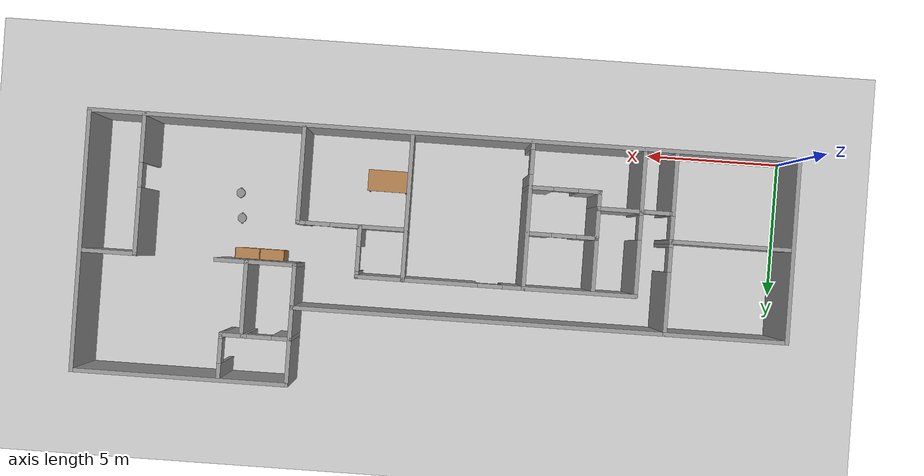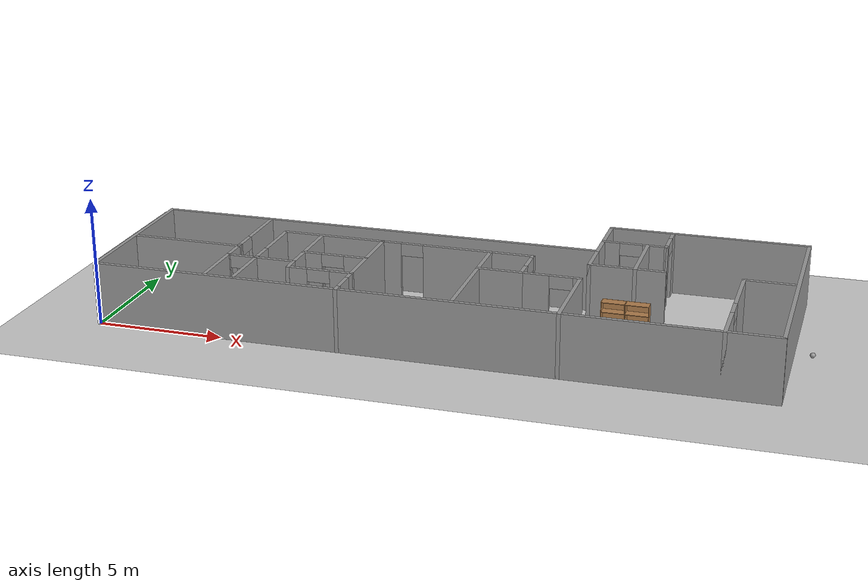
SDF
<sdf version="1.6">
 <world name="default">
  <plugin name="hello" filename="libhello.so"/>
  <light name="sun" type="directional">
   <pose>0 0 10 0 -0 0</pose>
   <diffuse>0.8 0.8 0.8 1</diffuse>
   <specular>0.2 0.2 0.2 1</specular>
   <attenuation>
    <range>1000</range>
    <constant>0.9</constant>
    <linear>0.01</linear>
    <quadratic>0.001</quadratic>
   </attenuation>
   <direction>-0.5 0.1 -0.9</direction>
  </light>
  <model name="ground_plane">
   <static>1</static>
   <link name="link">
    <collision name="collision">
     <geometry><plane><normal>0 0 1</normal><size>100 100</size></plane></geometry>
     <surface>
      <contact><collide_bitmask>65535</collide_bitmask></contact>
      <friction><ode><mu>100</mu><mu2>50</mu2></ode></friction>
     </surface>
    </collision>
    <visual name="visual">
     <cast_shadows>0</cast_shadows>
     <geometry><plane><normal>0 0 1</normal><size>100 100</size></plane></geometry>
     <material>
      <script><uri>file://media/materials/scripts/gazebo.material</uri><name>Gazebo/Grey</name></script>
     </material>
    </visual>
   </link>
  </model>
  <gravity>0 0 -9.8</gravity>
  <magnetic_field>6e-06 2.3e-05 -4.2e-05</magnetic_field>
  <atmosphere type="adiabatic"/>
  <physics name="default_physics" default="0" type="ode">
   <max_step_size>0.001</max_step_size>
   <real_time_factor>1</real_time_factor>
   <real_time_update_rate>1000</real_time_update_rate>
  </physics>
  <scene><ambient>0.4 0.4 0.4 1</ambient><background>0.7 0.7 0.7 1</background><shadows>1</shadows></scene>
  <spherical_coordinates>
   <surface_model>EARTH_WGS84</surface_model>
   <latitude_deg>0</latitude_deg>
   <longitude_deg>0</longitude_deg>
   <elevation>0</elevation>
   <heading_deg>0</heading_deg>
  </spherical_coordinates>
  <model name="myBuilding">
   <pose>12.88 4.72 0 0 -0 0</pose>
   <link name="Wall_13">
    <collision name="Wall_13_Collision">
     <geometry><box><size>6.78 0.15 2.5</size></box></geometry>
     <pose>0 0 1.25 0 -0 0</pose>
    </collision>
    <visual name="Wall_13_Visual">
     <pose>0 0 1.25 0 -0 0</pose>
     <geometry><box><size>6.78 0.15 2.5</size></box></geometry>
     <material>
      <script><uri>file://media/materials/scripts/gazebo.material</uri><name>Gazebo/Grey</name></script>
      <ambient>1 1 1 1</ambient>
     </material>
     <meta><layer>0</layer></meta>
    </visual>
    <pose>-12.88 -1.405 0 0 -0 1.5708</pose>
   </link>
   <link name="Wall_17">
    <collision name="Wall_17_Collision">
     <geometry><box><size>9.5 0.15 2.5</size></box></geometry>
     <pose>0 0 1.25 0 -0 0</pose>
    </collision>
    <visual name="Wall_17_Visual">
     <pose>0 0 1.25 0 -0 0</pose>
     <geometry><box><size>9.5 0.15 2.5</size></box></geometry>
     <material>
      <script><uri>file://media/materials/scripts/gazebo.material</uri><name>Gazebo/Grey</name></script>
      <ambient>1 1 1 1</ambient>
     </material>
     <meta><layer>0</layer></meta>
    </visual>
    <pose>12.88 0.045 0 0 0 -1.5708</pose>
   </link>
   <link name="Wall_19">
    <collision name="Wall_19_Collision">
     <geometry><box><size>4.58 0.15 2.5</size></box></geometry>
     <pose>0 0 1.25 0 -0 0</pose>
    </collision>
    <visual name="Wall_19_Visual">
     <pose>0 0 1.25 0 -0 0</pose>
     <geometry><box><size>4.58 0.15 2.5</size></box></geometry>
     <material>
      <script><uri>file://media/materials/scripts/gazebo.material</uri><name>Gazebo/Grey</name></script>
      <ambient>1 1 1 1</ambient>
     </material>
     <meta><layer>0</layer></meta>
    </visual>
    <pose>-10.665 -1.45 0 0 -0 0</pose>
   </link>
   <link name="Wall_22">
    <pose>-8.45 -3.01 0 0 0 -1.5708</pose>
    <visual name="Wall_22_Visual_0">
     <pose>-1.57168 0 1.25 0 -0 0</pose>
     <geometry><box><size>0.126638 0.15 2.5</size></box></geometry>
     <material>
      <script><uri>file://media/materials/scripts/gazebo.material</uri><name>Gazebo/Grey</name></script>
      <ambient>1 1 1 1</ambient>
     </material>
     <meta><layer>0</layer></meta>
    </visual>
    <collision name="Wall_22_Collision_0">
     <geometry><box><size>0.126638 0.15 2.5</size></box></geometry>
     <pose>-1.57168 0 1.25 0 -0 0</pose>
    </collision>
    <visual name="Wall_22_Visual_1">
     <pose>0.503319 0 1.25 0 -0 0</pose>
     <geometry><box><size>2.26336 0.15 2.5</size></box></geometry>
     <material>
      <script><uri>file://media/materials/scripts/gazebo.material</uri><name>Gazebo/Grey</name></script>
      <ambient>1 1 1 1</ambient>
     </material>
     <meta><layer>0</layer></meta>
    </visual>
    <collision name="Wall_22_Collision_1">
     <geometry><box><size>2.26336 0.15 2.5</size></box></geometry>
     <pose>0.503319 0 1.25 0 -0 0</pose>
    </collision>
    <visual name="Wall_22_Visual_2">
     <pose>-1.06836 0 2.25 0 -0 0</pose>
     <geometry><box><size>0.88 0.15 0.5</size></box></geometry>
     <material>
      <script><uri>file://media/materials/scripts/gazebo.material</uri><name>Gazebo/Grey</name></script>
      <ambient>1 1 1 1</ambient>
     </material>
     <meta><layer>0</layer></meta>
    </visual>
    <collision name="Wall_22_Collision_2">
     <geometry><box><size>0.88 0.15 0.5</size></box></geometry>
     <pose>-1.06836 0 2.25 0 -0 0</pose>
    </collision>
   </link>
   <link name="Wall_24">
    <collision name="Wall_24_Collision">
     <geometry><box><size>4.58 0.15 2.5</size></box></geometry>
     <pose>0 0 1.25 0 -0 0</pose>
    </collision>
    <visual name="Wall_24_Visual">
     <pose>0 0 1.25 0 -0 0</pose>
     <geometry><box><size>4.58 0.15 2.5</size></box></geometry>
     <material>
      <script><uri>file://media/materials/scripts/gazebo.material</uri><name>Gazebo/Grey</name></script>
      <ambient>1 1 1 1</ambient>
     </material>
     <meta><layer>0</layer></meta>
    </visual>
    <pose>-10.665 1.91 0 0 -0 0</pose>
   </link>
   <link name="Wall_28">
    <pose>-8.45 0.23 0 0 0 -1.5708</pose>
    <visual name="Wall_28_Visual_0">
     <pose>-0.591583 0 1.25 0 -0 0</pose>
     <geometry><box><size>2.32683 0.15 2.5</size></box></geometry>
     <material>
      <script><uri>file://media/materials/scripts/gazebo.material</uri><name>Gazebo/Grey</name></script>
      <ambient>1 1 1 1</ambient>
     </material>
     <meta><layer>0</layer></meta>
    </visual>
    <collision name="Wall_28_Collision_0">
     <geometry><box><size>2.32683 0.15 2.5</size></box></geometry>
     <pose>-0.591583 0 1.25 0 -0 0</pose>
    </collision>
    <visual name="Wall_28_Visual_1">
     <pose>1.61342 0 1.25 0 -0 0</pose>
     <geometry><box><size>0.283165 0.15 2.5</size></box></geometry>
     <material>
      <script><uri>file://media/materials/scripts/gazebo.material</uri><name>Gazebo/Grey</name></script>
      <ambient>1 1 1 1</ambient>
     </material>
     <meta><layer>0</layer></meta>
    </visual>
    <collision name="Wall_28_Collision_1">
     <geometry><box><size>0.283165 0.15 2.5</size></box></geometry>
     <pose>1.61342 0 1.25 0 -0 0</pose>
    </collision>
    <visual name="Wall_28_Visual_2">
     <pose>1.02184 0 2.25 0 -0 0</pose>
     <geometry><box><size>0.9 0.15 0.5</size></box></geometry>
     <material>
      <script><uri>file://media/materials/scripts/gazebo.material</uri><name>Gazebo/Grey</name></script>
      <ambient>1 1 1 1</ambient>
     </material>
     <meta><layer>0</layer></meta>
    </visual>
    <collision name="Wall_28_Collision_2">
     <geometry><box><size>0.9 0.15 0.5</size></box></geometry>
     <pose>1.02184 0 2.25 0 -0 0</pose>
    </collision>
   </link>
   <link name="Wall_30">
    <pose>-7.3 -2.05 0 0 0 -1.5708</pose>
    <visual name="Wall_30_Visual_0">
     <pose>-1.68457 0 1.25 0 -0 0</pose>
     <geometry><box><size>2.12087 0.15 2.5</size></box></geometry>
     <material>
      <script><uri>file://media/materials/scripts/gazebo.material</uri><name>Gazebo/Grey</name></script>
      <ambient>1 1 1 1</ambient>
     </material>
     <meta><layer>0</layer></meta>
    </visual>
    <collision name="Wall_30_Collision_0">
     <geometry><box><size>2.12087 0.15 2.5</size></box></geometry>
     <pose>-1.68457 0 1.25 0 -0 0</pose>
    </collision>
    <visual name="Wall_30_Visual_1">
     <pose>1.51043 0 1.25 0 -0 0</pose>
     <geometry><box><size>2.46913 0.15 2.5</size></box></geometry>
     <material>
      <script><uri>file://media/materials/scripts/gazebo.material</uri><name>Gazebo/Grey</name></script>
      <ambient>1 1 1 1</ambient>
     </material>
     <meta><layer>0</layer></meta>
    </visual>
    <collision name="Wall_30_Collision_1">
     <geometry><box><size>2.46913 0.15 2.5</size></box></geometry>
     <pose>1.51043 0 1.25 0 -0 0</pose>
    </collision>
    <visual name="Wall_30_Visual_2">
     <pose>-0.174131 0 2.25 0 -0 0</pose>
     <geometry><box><size>0.9 0.15 0.5</size></box></geometry>
     <material>
      <script><uri>file://media/materials/scripts/gazebo.material</uri><name>Gazebo/Grey</name></script>
      <ambient>1 1 1 1</ambient>
     </material>
     <meta><layer>0</layer></meta>
    </visual>
    <collision name="Wall_30_Collision_2">
     <geometry><box><size>0.9 0.15 0.5</size></box></geometry>
     <pose>-0.174131 0 2.25 0 -0 0</pose>
    </collision>
   </link>
   <link name="Wall_36">
    <collision name="Wall_36_Collision">
     <geometry><box><size>4.22 0.15 2.5</size></box></geometry>
     <pose>0 0 1.25 0 -0 0</pose>
    </collision>
    <visual name="Wall_36_Visual">
     <pose>0 0 1.25 0 -0 0</pose>
     <geometry><box><size>4.22 0.15 2.5</size></box></geometry>
     <material>
      <script><uri>file://media/materials/scripts/gazebo.material</uri><name>Gazebo/Grey</name></script>
      <ambient>1 1 1 1</ambient>
     </material>
     <meta><layer>0</layer></meta>
    </visual>
    <pose>-5.265 0.62 0 0 -0 0</pose>
   </link>
   <link name="Wall_38">
    <pose>-3.23 -2.05 0 0 0 -1.5708</pose>
    <visual name="Wall_38_Visual_0">
     <pose>-0.635523 0 1.25 0 -0 0</pose>
     <geometry><box><size>4.21895 0.15 2.5</size></box></geometry>
     <material>
      <script><uri>file://media/materials/scripts/gazebo.material</uri><name>Gazebo/Grey</name></script>
      <ambient>1 1 1 1</ambient>
     </material>
     <meta><layer>0</layer></meta>
    </visual>
    <collision name="Wall_38_Collision_0">
     <geometry><box><size>4.21895 0.15 2.5</size></box></geometry>
     <pose>-0.635523 0 1.25 0 -0 0</pose>
    </collision>
    <visual name="Wall_38_Visual_1">
     <pose>2.55948 0 1.25 0 -0 0</pose>
     <geometry><box><size>0.371046 0.15 2.5</size></box></geometry>
     <material>
      <script><uri>file://media/materials/scripts/gazebo.material</uri><name>Gazebo/Grey</name></script>
      <ambient>1 1 1 1</ambient>
     </material>
     <meta><layer>0</layer></meta>
    </visual>
    <collision name="Wall_38_Collision_1">
     <geometry><box><size>0.371046 0.15 2.5</size></box></geometry>
     <pose>2.55948 0 1.25 0 -0 0</pose>
    </collision>
    <visual name="Wall_38_Visual_2">
     <pose>1.92395 0 2.25 0 -0 0</pose>
     <geometry><box><size>0.9 0.15 0.5</size></box></geometry>
     <material>
      <script><uri>file://media/materials/scripts/gazebo.material</uri><name>Gazebo/Grey</name></script>
      <ambient>1 1 1 1</ambient>
     </material>
     <meta><layer>0</layer></meta>
    </visual>
    <collision name="Wall_38_Collision_2">
     <geometry><box><size>0.9 0.15 0.5</size></box></geometry>
     <pose>1.92395 0 2.25 0 -0 0</pose>
    </collision>
   </link>
   <link name="Wall_42">
    <pose>-1.04 0.62 0 0 -0 0</pose>
    <visual name="Wall_42_Visual_0">
     <pose>-1.84475 0 1.25 0 -0 0</pose>
     <geometry><box><size>0.840504 0.15 2.5</size></box></geometry>
     <material>
      <script><uri>file://media/materials/scripts/gazebo.material</uri><name>Gazebo/Grey</name></script>
      <ambient>1 1 1 1</ambient>
     </material>
     <meta><layer>0</layer></meta>
    </visual>
    <collision name="Wall_42_Collision_0">
     <geometry><box><size>0.840504 0.15 2.5</size></box></geometry>
     <pose>-1.84475 0 1.25 0 -0 0</pose>
    </collision>
    <visual name="Wall_42_Visual_1">
     <pose>0.870252 0 1.25 0 -0 0</pose>
     <geometry><box><size>2.7895 0.15 2.5</size></box></geometry>
     <material>
      <script><uri>file://media/materials/scripts/gazebo.material</uri><name>Gazebo/Grey</name></script>
      <ambient>1 1 1 1</ambient>
     </material>
     <meta><layer>0</layer></meta>
    </visual>
    <collision name="Wall_42_Collision_1">
     <geometry><box><size>2.7895 0.15 2.5</size></box></geometry>
     <pose>0.870252 0 1.25 0 -0 0</pose>
    </collision>
    <visual name="Wall_42_Visual_2">
     <pose>-0.974496 0 2.25 0 -0 0</pose>
     <geometry><box><size>0.9 0.15 0.5</size></box></geometry>
     <material>
      <script><uri>file://media/materials/scripts/gazebo.material</uri><name>Gazebo/Grey</name></script>
      <ambient>1 1 1 1</ambient>
     </material>
     <meta><layer>0</layer></meta>
    </visual>
    <collision name="Wall_42_Collision_2">
     <geometry><box><size>0.9 0.15 0.5</size></box></geometry>
     <pose>-0.974496 0 2.25 0 -0 0</pose>
    </collision>
   </link>
   <link name="Wall_44">
    <collision name="Wall_44_Collision">
     <geometry><box><size>5.34 0.15 2.5</size></box></geometry>
     <pose>0 0 1.25 0 -0 0</pose>
    </collision>
    <visual name="Wall_44_Visual">
     <pose>0 0 1.25 0 -0 0</pose>
     <geometry><box><size>5.34 0.15 2.5</size></box></geometry>
     <material>
      <script><uri>file://media/materials/scripts/gazebo.material</uri><name>Gazebo/Grey</name></script>
      <ambient>1 1 1 1</ambient>
     </material>
     <meta><layer>0</layer></meta>
    </visual>
    <pose>1.15 -1.975 0 0 0 -1.5708</pose>
   </link>
   <link name="Wall_46">
    <collision name="Wall_46_Collision">
     <geometry><box><size>1.7 0.15 2.5</size></box></geometry>
     <pose>0 0 1.25 0 -0 0</pose>
    </collision>
    <visual name="Wall_46_Visual">
     <pose>0 0 1.25 0 -0 0</pose>
     <geometry><box><size>1.7 0.15 2.5</size></box></geometry>
     <material>
      <script><uri>file://media/materials/scripts/gazebo.material</uri><name>Gazebo/Grey</name></script>
      <ambient>1 1 1 1</ambient>
     </material>
     <meta><layer>0</layer></meta>
    </visual>
    <pose>-6.525 -2.46 0 0 -0 0</pose>
   </link>
   <link name="Wall_48">
    <collision name="Wall_48_Collision">
     <geometry><box><size>3.08 0.15 2.5</size></box></geometry>
     <pose>0 0 1.25 0 -0 0</pose>
    </collision>
    <visual name="Wall_48_Visual">
     <pose>0 0 1.25 0 -0 0</pose>
     <geometry><box><size>3.08 0.15 2.5</size></box></geometry>
     <material>
      <script><uri>file://media/materials/scripts/gazebo.material</uri><name>Gazebo/Grey</name></script>
      <ambient>1 1 1 1</ambient>
     </material>
     <meta><layer>0</layer></meta>
    </visual>
    <pose>-5.75 -0.995 0 0 -0 1.5708</pose>
   </link>
   <link name="Wall_5">
    <collision name="Wall_5_Collision">
     <geometry><box><size>25.91 0.15 2.5</size></box></geometry>
     <pose>0 0 1.25 0 -0 0</pose>
    </collision>
    <visual name="Wall_5_Visual">
     <pose>0 0 1.25 0 -0 0</pose>
     <geometry><box><size>25.91 0.15 2.5</size></box></geometry>
     <material>
      <script><uri>file://media/materials/scripts/gazebo.material</uri><name>Gazebo/Grey</name></script>
      <ambient>1 1 1 1</ambient>
     </material>
     <meta><layer>0</layer></meta>
    </visual>
    <pose>0 -4.72 0 0 -0 0</pose>
   </link>
   <link name="Wall_50">
    <pose>-7.84 -2.46 0 0 -0 3.14159</pose>
    <visual name="Wall_50_Visual_0">
     <pose>-0.514098 0 1.25 0 -0 0</pose>
     <geometry><box><size>0.201804 0.15 2.5</size></box></geometry>
     <material>
      <script><uri>file://media/materials/scripts/gazebo.material</uri><name>Gazebo/Grey</name></script>
      <ambient>1 1 1 1</ambient>
     </material>
     <meta><layer>0</layer></meta>
    </visual>
    <collision name="Wall_50_Collision_0">
     <geometry><box><size>0.201804 0.15 2.5</size></box></geometry>
     <pose>-0.514098 0 1.25 0 -0 0</pose>
    </collision>
    <visual name="Wall_50_Visual_1">
     <pose>0.550902 0 1.25 0 -0 0</pose>
     <geometry><box><size>0.128196 0.15 2.5</size></box></geometry>
     <material>
      <script><uri>file://media/materials/scripts/gazebo.material</uri><name>Gazebo/Grey</name></script>
      <ambient>1 1 1 1</ambient>
     </material>
     <meta><layer>0</layer></meta>
    </visual>
    <collision name="Wall_50_Collision_1">
     <geometry><box><size>0.128196 0.15 2.5</size></box></geometry>
     <pose>0.550902 0 1.25 0 -0 0</pose>
    </collision>
    <visual name="Wall_50_Visual_2">
     <pose>0.036804 0 2.25 0 -0 0</pose>
     <geometry><box><size>0.9 0.15 0.5</size></box></geometry>
     <material>
      <script><uri>file://media/materials/scripts/gazebo.material</uri><name>Gazebo/Grey</name></script>
      <ambient>1 1 1 1</ambient>
     </material>
     <meta><layer>0</layer></meta>
    </visual>
    <collision name="Wall_50_Collision_2">
     <geometry><box><size>0.9 0.15 0.5</size></box></geometry>
     <pose>0.036804 0 2.25 0 -0 0</pose>
    </collision>
   </link>
   <link name="Wall_52">
    <collision name="Wall_52_Collision">
     <geometry><box><size>1.82 0.15 2.5</size></box></geometry>
     <pose>0 0 1.25 0 -0 0</pose>
    </collision>
    <visual name="Wall_52_Visual">
     <pose>0 0 1.25 0 -0 0</pose>
     <geometry><box><size>1.82 0.15 2.5</size></box></geometry>
     <material>
      <script><uri>file://media/materials/scripts/gazebo.material</uri><name>Gazebo/Grey</name></script>
      <ambient>1 1 1 1</ambient>
     </material>
     <meta><layer>0</layer></meta>
    </visual>
    <pose>1.985 0.62 0 0 -0 0</pose>
   </link>
   <link name="Wall_54">
    <pose>2.82 -0.285 0 0 0 -1.5708</pose>
    <visual name="Wall_54_Visual_0">
     <pose>-0.847616 0 1.25 0 -0 0</pose>
     <geometry><box><size>0.264769 0.15 2.5</size></box></geometry>
     <material>
      <script><uri>file://media/materials/scripts/gazebo.material</uri><name>Gazebo/Grey</name></script>
      <ambient>1 1 1 1</ambient>
     </material>
     <meta><layer>0</layer></meta>
    </visual>
    <collision name="Wall_54_Collision_0">
     <geometry><box><size>0.264769 0.15 2.5</size></box></geometry>
     <pose>-0.847616 0 1.25 0 -0 0</pose>
    </collision>
    <visual name="Wall_54_Visual_1">
     <pose>0.582384 0 1.25 0 -0 0</pose>
     <geometry><box><size>0.795231 0.15 2.5</size></box></geometry>
     <material>
      <script><uri>file://media/materials/scripts/gazebo.material</uri><name>Gazebo/Grey</name></script>
      <ambient>1 1 1 1</ambient>
     </material>
     <meta><layer>0</layer></meta>
    </visual>
    <collision name="Wall_54_Collision_1">
     <geometry><box><size>0.795231 0.15 2.5</size></box></geometry>
     <pose>0.582384 0 1.25 0 -0 0</pose>
    </collision>
    <visual name="Wall_54_Visual_2">
     <pose>-0.265231 0 2.25 0 -0 0</pose>
     <geometry><box><size>0.9 0.15 0.5</size></box></geometry>
     <material>
      <script><uri>file://media/materials/scripts/gazebo.material</uri><name>Gazebo/Grey</name></script>
      <ambient>1 1 1 1</ambient>
     </material>
     <meta><layer>0</layer></meta>
    </visual>
    <collision name="Wall_54_Collision_2">
     <geometry><box><size>0.9 0.15 0.5</size></box></geometry>
     <pose>-0.265231 0 2.25 0 -0 0</pose>
    </collision>
   </link>
   <link name="Wall_56">
    <collision name="Wall_56_Collision">
     <geometry><box><size>1.82 0.15 2.5</size></box></geometry>
     <pose>0 0 1.25 0 -0 0</pose>
    </collision>
    <visual name="Wall_56_Visual">
     <pose>0 0 1.25 0 -0 0</pose>
     <geometry><box><size>1.82 0.15 2.5</size></box></geometry>
     <material>
      <script><uri>file://media/materials/scripts/gazebo.material</uri><name>Gazebo/Grey</name></script>
      <ambient>1 1 1 1</ambient>
     </material>
     <meta><layer>0</layer></meta>
    </visual>
    <pose>1.985 -1.19 0 0 -0 3.14159</pose>
   </link>
   <link name="Wall_58">
    <pose>3.95 -1.19 0 0 -0 0</pose>
    <visual name="Wall_58_Visual_0">
     <pose>-0.625709 0 1.25 0 -0 0</pose>
     <geometry><box><size>1.15858 0.15 2.5</size></box></geometry>
     <material>
      <script><uri>file://media/materials/scripts/gazebo.material</uri><name>Gazebo/Grey</name></script>
      <ambient>1 1 1 1</ambient>
     </material>
     <meta><layer>0</layer></meta>
    </visual>
    <collision name="Wall_58_Collision_0">
     <geometry><box><size>1.15858 0.15 2.5</size></box></geometry>
     <pose>-0.625709 0 1.25 0 -0 0</pose>
    </collision>
    <visual name="Wall_58_Visual_1">
     <pose>1.02929 0 1.25 0 -0 0</pose>
     <geometry><box><size>0.351418 0.15 2.5</size></box></geometry>
     <material>
      <script><uri>file://media/materials/scripts/gazebo.material</uri><name>Gazebo/Grey</name></script>
      <ambient>1 1 1 1</ambient>
     </material>
     <meta><layer>0</layer></meta>
    </visual>
    <collision name="Wall_58_Collision_1">
     <geometry><box><size>0.351418 0.15 2.5</size></box></geometry>
     <pose>1.02929 0 1.25 0 -0 0</pose>
    </collision>
    <visual name="Wall_58_Visual_2">
     <pose>0.403582 0 2.25 0 -0 0</pose>
     <geometry><box><size>0.9 0.15 0.5</size></box></geometry>
     <material>
      <script><uri>file://media/materials/scripts/gazebo.material</uri><name>Gazebo/Grey</name></script>
      <ambient>1 1 1 1</ambient>
     </material>
     <meta><layer>0</layer></meta>
    </visual>
    <collision name="Wall_58_Collision_2">
     <geometry><box><size>0.9 0.15 0.5</size></box></geometry>
     <pose>0.403582 0 2.25 0 -0 0</pose>
    </collision>
   </link>
   <link name="Wall_60">
    <collision name="Wall_60_Collision">
     <geometry><box><size>3.68 0.15 2.5</size></box></geometry>
     <pose>0 0 1.25 0 -0 0</pose>
    </collision>
    <visual name="Wall_60_Visual">
     <pose>0 0 1.25 0 -0 0</pose>
     <geometry><box><size>3.68 0.15 2.5</size></box></geometry>
     <material>
      <script><uri>file://media/materials/scripts/gazebo.material</uri><name>Gazebo/Grey</name></script>
      <ambient>1 1 1 1</ambient>
     </material>
     <meta><layer>0</layer></meta>
    </visual>
    <pose>5.08 -2.955 0 0 0 -1.5708</pose>
   </link>
   <link name="Wall_62">
    <collision name="Wall_62_Collision">
     <geometry><box><size>13.68 0.15 2.5</size></box></geometry>
     <pose>0 0 1.25 0 -0 0</pose>
    </collision>
    <visual name="Wall_62_Visual">
     <pose>0 0 1.25 0 -0 0</pose>
     <geometry><box><size>13.68 0.15 2.5</size></box></geometry>
     <material>
      <script><uri>file://media/materials/scripts/gazebo.material</uri><name>Gazebo/Grey</name></script>
      <ambient>1 1 1 1</ambient>
     </material>
     <meta><layer>0</layer></meta>
    </visual>
    <pose>-1.685 1.91 0 0 -0 0</pose>
   </link>
   <link name="Wall_64">
    <collision name="Wall_64_Collision">
     <geometry><box><size>2.96 0.15 2.5</size></box></geometry>
     <pose>0 0 1.25 0 -0 0</pose>
    </collision>
    <visual name="Wall_64_Visual">
     <pose>0 0 1.25 0 -0 0</pose>
     <geometry><box><size>2.96 0.15 2.5</size></box></geometry>
     <material>
      <script><uri>file://media/materials/scripts/gazebo.material</uri><name>Gazebo/Grey</name></script>
      <ambient>1 1 1 1</ambient>
     </material>
     <meta><layer>0</layer></meta>
    </visual>
    <pose>5.08 3.315 0 0 -0 1.5708</pose>
   </link>
   <link name="Wall_66">
    <collision name="Wall_66_Collision">
     <geometry><box><size>7.95 0.15 2.5</size></box></geometry>
     <pose>0 0 1.25 0 -0 0</pose>
    </collision>
    <visual name="Wall_66_Visual">
     <pose>0 0 1.25 0 -0 0</pose>
     <geometry><box><size>7.95 0.15 2.5</size></box></geometry>
     <material>
      <script><uri>file://media/materials/scripts/gazebo.material</uri><name>Gazebo/Grey</name></script>
      <ambient>1 1 1 1</ambient>
     </material>
     <meta><layer>0</layer></meta>
    </visual>
    <pose>8.98 4.72 0 0 -0 0</pose>
   </link>
   <link name="Wall_70">
    <collision name="Wall_70_Collision">
     <geometry><box><size>1.69 0.15 2.5</size></box></geometry>
     <pose>0 0 1.25 0 -0 0</pose>
    </collision>
    <visual name="Wall_70_Visual">
     <pose>0 0 1.25 0 -0 0</pose>
     <geometry><box><size>1.69 0.15 2.5</size></box></geometry>
     <material>
      <script><uri>file://media/materials/scripts/gazebo.material</uri><name>Gazebo/Grey</name></script>
      <ambient>1 1 1 1</ambient>
     </material>
     <meta><layer>0</layer></meta>
    </visual>
    <pose>5.08 1.14 0 0 -0 1.5708</pose>
   </link>
   <link name="Wall_73">
    <pose>-4.49 -1.38 0 0 -0 0</pose>
    <visual name="Wall_73_Visual_0">
     <pose>-0.930662 0 1.25 0 -0 0</pose>
     <geometry><box><size>0.808676 0.15 2.5</size></box></geometry>
     <material>
      <script><uri>file://media/materials/scripts/gazebo.material</uri><name>Gazebo/Grey</name></script>
      <ambient>1 1 1 1</ambient>
     </material>
     <meta><layer>0</layer></meta>
    </visual>
    <collision name="Wall_73_Collision_0">
     <geometry><box><size>0.808676 0.15 2.5</size></box></geometry>
     <pose>-0.930662 0 1.25 0 -0 0</pose>
    </collision>
    <visual name="Wall_73_Visual_1">
     <pose>0.854338 0 1.25 0 -0 0</pose>
     <geometry><box><size>0.961324 0.15 2.5</size></box></geometry>
     <material>
      <script><uri>file://media/materials/scripts/gazebo.material</uri><name>Gazebo/Grey</name></script>
      <ambient>1 1 1 1</ambient>
     </material>
     <meta><layer>0</layer></meta>
    </visual>
    <collision name="Wall_73_Collision_1">
     <geometry><box><size>0.961324 0.15 2.5</size></box></geometry>
     <pose>0.854338 0 1.25 0 -0 0</pose>
    </collision>
    <visual name="Wall_73_Visual_2">
     <pose>-0.076324 0 2.25 0 -0 0</pose>
     <geometry><box><size>0.9 0.15 0.5</size></box></geometry>
     <material>
      <script><uri>file://media/materials/scripts/gazebo.material</uri><name>Gazebo/Grey</name></script>
      <ambient>1 1 1 1</ambient>
     </material>
     <meta><layer>0</layer></meta>
    </visual>
    <collision name="Wall_73_Collision_2">
     <geometry><box><size>0.9 0.15 0.5</size></box></geometry>
     <pose>-0.076324 0 2.25 0 -0 0</pose>
    </collision>
   </link>
   <link name="Wall_75">
    <pose>-4.49 -3.05 0 0 -0 0</pose>
    <visual name="Wall_75_Visual_0">
     <pose>-0.907672 0 1.25 0 -0 0</pose>
     <geometry><box><size>0.854655 0.15 2.5</size></box></geometry>
     <material>
      <script><uri>file://media/materials/scripts/gazebo.material</uri><name>Gazebo/Grey</name></script>
      <ambient>1 1 1 1</ambient>
     </material>
     <meta><layer>0</layer></meta>
    </visual>
    <collision name="Wall_75_Collision_0">
     <geometry><box><size>0.854655 0.15 2.5</size></box></geometry>
     <pose>-0.907672 0 1.25 0 -0 0</pose>
    </collision>
    <visual name="Wall_75_Visual_1">
     <pose>0.877328 0 1.25 0 -0 0</pose>
     <geometry><box><size>0.915345 0.15 2.5</size></box></geometry>
     <material>
      <script><uri>file://media/materials/scripts/gazebo.material</uri><name>Gazebo/Grey</name></script>
      <ambient>1 1 1 1</ambient>
     </material>
     <meta><layer>0</layer></meta>
    </visual>
    <collision name="Wall_75_Collision_1">
     <geometry><box><size>0.915345 0.15 2.5</size></box></geometry>
     <pose>0.877328 0 1.25 0 -0 0</pose>
    </collision>
    <visual name="Wall_75_Visual_2">
     <pose>-0.030345 0 2.25 0 -0 0</pose>
     <geometry><box><size>0.9 0.15 0.5</size></box></geometry>
     <material>
      <script><uri>file://media/materials/scripts/gazebo.material</uri><name>Gazebo/Grey</name></script>
      <ambient>1 1 1 1</ambient>
     </material>
     <meta><layer>0</layer></meta>
    </visual>
    <collision name="Wall_75_Collision_2">
     <geometry><box><size>0.9 0.15 0.5</size></box></geometry>
     <pose>-0.030345 0 2.25 0 -0 0</pose>
    </collision>
   </link>
   <link name="Wall_77">
    <collision name="Wall_77_Collision">
     <geometry><box><size>0.74 0.15 2.5</size></box></geometry>
     <pose>0 0 1.25 0 -0 0</pose>
    </collision>
    <visual name="Wall_77_Visual">
     <pose>0 0 1.25 0 -0 0</pose>
     <geometry><box><size>0.74 0.15 2.5</size></box></geometry>
     <material>
      <script><uri>file://media/materials/scripts/gazebo.material</uri><name>Gazebo/Grey</name></script>
      <ambient>1 1 1 1</ambient>
     </material>
     <meta><layer>0</layer></meta>
    </visual>
    <pose>-5.75 -2.755 0 0 0 -1.5708</pose>
   </link>
   <link name="Wall_79">
    <pose>6.32 3.06 0 0 -0 0</pose>
    <visual name="Wall_79_Visual_0">
     <pose>-0.951896 0 1.25 0 -0 0</pose>
     <geometry><box><size>0.726208 0.15 2.5</size></box></geometry>
     <material>
      <script><uri>file://media/materials/scripts/gazebo.material</uri><name>Gazebo/Grey</name></script>
      <ambient>1 1 1 1</ambient>
     </material>
     <meta><layer>0</layer></meta>
    </visual>
    <collision name="Wall_79_Collision_0">
     <geometry><box><size>0.726208 0.15 2.5</size></box></geometry>
     <pose>-0.951896 0 1.25 0 -0 0</pose>
    </collision>
    <visual name="Wall_79_Visual_1">
     <pose>0.813104 0 1.25 0 -0 0</pose>
     <geometry><box><size>1.00379 0.15 2.5</size></box></geometry>
     <material>
      <script><uri>file://media/materials/scripts/gazebo.material</uri><name>Gazebo/Grey</name></script>
      <ambient>1 1 1 1</ambient>
     </material>
     <meta><layer>0</layer></meta>
    </visual>
    <collision name="Wall_79_Collision_1">
     <geometry><box><size>1.00379 0.15 2.5</size></box></geometry>
     <pose>0.813104 0 1.25 0 -0 0</pose>
    </collision>
    <visual name="Wall_79_Visual_2">
     <pose>-0.138792 0 2.25 0 -0 0</pose>
     <geometry><box><size>0.9 0.15 0.5</size></box></geometry>
     <material>
      <script><uri>file://media/materials/scripts/gazebo.material</uri><name>Gazebo/Grey</name></script>
      <ambient>1 1 1 1</ambient>
     </material>
     <meta><layer>0</layer></meta>
    </visual>
    <collision name="Wall_79_Collision_2">
     <geometry><box><size>0.9 0.15 0.5</size></box></geometry>
     <pose>-0.138792 0 2.25 0 -0 0</pose>
    </collision>
   </link>
   <link name="Wall_81">
    <pose>7.56 3.815 0 0 -0 1.5708</pose>
    <visual name="Wall_81_Visual_0">
     <pose>-0.716566 0 1.25 0 -0 0</pose>
     <geometry><box><size>0.226868 0.15 2.5</size></box></geometry>
     <material>
      <script><uri>file://media/materials/scripts/gazebo.material</uri><name>Gazebo/Grey</name></script>
      <ambient>1 1 1 1</ambient>
     </material>
     <meta><layer>0</layer></meta>
    </visual>
    <collision name="Wall_81_Collision_0">
     <geometry><box><size>0.226868 0.15 2.5</size></box></geometry>
     <pose>-0.716566 0 1.25 0 -0 0</pose>
    </collision>
    <visual name="Wall_81_Visual_1">
     <pose>0.563434 0 1.25 0 -0 0</pose>
     <geometry><box><size>0.533132 0.15 2.5</size></box></geometry>
     <material>
      <script><uri>file://media/materials/scripts/gazebo.material</uri><name>Gazebo/Grey</name></script>
      <ambient>1 1 1 1</ambient>
     </material>
     <meta><layer>0</layer></meta>
    </visual>
    <collision name="Wall_81_Collision_1">
     <geometry><box><size>0.533132 0.15 2.5</size></box></geometry>
     <pose>0.563434 0 1.25 0 -0 0</pose>
    </collision>
    <visual name="Wall_81_Visual_2">
     <pose>-0.153132 0 2.25 0 -0 0</pose>
     <geometry><box><size>0.9 0.15 0.5</size></box></geometry>
     <material>
      <script><uri>file://media/materials/scripts/gazebo.material</uri><name>Gazebo/Grey</name></script>
      <ambient>1 1 1 1</ambient>
     </material>
     <meta><layer>0</layer></meta>
    </visual>
    <collision name="Wall_81_Collision_2">
     <geometry><box><size>0.9 0.15 0.5</size></box></geometry>
     <pose>-0.153132 0 2.25 0 -0 0</pose>
    </collision>
   </link>
   <link name="Wall_83">
    <collision name="Wall_83_Collision">
     <geometry><box><size>2.84 0.15 2.5</size></box></geometry>
     <pose>0 0 1.25 0 -0 0</pose>
    </collision>
    <visual name="Wall_83_Visual">
     <pose>0 0 1.25 0 -0 0</pose>
     <geometry><box><size>2.84 0.15 2.5</size></box></geometry>
     <material>
      <script><uri>file://media/materials/scripts/gazebo.material</uri><name>Gazebo/Grey</name></script>
      <ambient>1 1 1 1</ambient>
     </material>
     <meta><layer>0</layer></meta>
    </visual>
    <pose>6.83 1.715 0 0 0 -1.5708</pose>
   </link>
   <link name="Wall_85">
    <pose>10.88 -2.175 0 0 -0 1.5708</pose>
    <visual name="Wall_85_Visual_0">
     <pose>-1.69586 0 1.25 0 -0 0</pose>
     <geometry><box><size>1.84828 0.15 2.5</size></box></geometry>
     <material>
      <script><uri>file://media/materials/scripts/gazebo.material</uri><name>Gazebo/Grey</name></script>
      <ambient>1 1 1 1</ambient>
     </material>
     <meta><layer>0</layer></meta>
    </visual>
    <collision name="Wall_85_Collision_0">
     <geometry><box><size>1.84828 0.15 2.5</size></box></geometry>
     <pose>-1.69586 0 1.25 0 -0 0</pose>
    </collision>
    <visual name="Wall_85_Visual_1">
     <pose>1.37414 0 1.25 0 -0 0</pose>
     <geometry><box><size>2.49172 0.15 2.5</size></box></geometry>
     <material>
      <script><uri>file://media/materials/scripts/gazebo.material</uri><name>Gazebo/Grey</name></script>
      <ambient>1 1 1 1</ambient>
     </material>
     <meta><layer>0</layer></meta>
    </visual>
    <collision name="Wall_85_Collision_1">
     <geometry><box><size>2.49172 0.15 2.5</size></box></geometry>
     <pose>1.37414 0 1.25 0 -0 0</pose>
    </collision>
    <visual name="Wall_85_Visual_2">
     <pose>-0.321716 0 2.25 0 -0 0</pose>
     <geometry><box><size>0.9 0.15 0.5</size></box></geometry>
     <material>
      <script><uri>file://media/materials/scripts/gazebo.material</uri><name>Gazebo/Grey</name></script>
      <ambient>1 1 1 1</ambient>
     </material>
     <meta><layer>0</layer></meta>
    </visual>
    <collision name="Wall_85_Collision_2">
     <geometry><box><size>0.9 0.15 0.5</size></box></geometry>
     <pose>-0.321716 0 2.25 0 -0 0</pose>
    </collision>
   </link>
   <link name="Wall_87">
    <collision name="Wall_87_Collision">
     <geometry><box><size>3 0.15 2.5</size></box></geometry>
     <pose>0 0 1.25 0 -0 0</pose>
    </collision>
    <visual name="Wall_87_Visual">
     <pose>0 0 1.25 0 -0 0</pose>
     <geometry><box><size>3 0.15 2.5</size></box></geometry>
     <material>
      <script><uri>file://media/materials/scripts/gazebo.material</uri><name>Gazebo/Grey</name></script>
      <ambient>1 1 1 1</ambient>
     </material>
     <meta><layer>0</layer></meta>
    </visual>
    <pose>6.505 0.37 0 0 -0 0</pose>
   </link>
   <link name="Wall_89">
    <collision name="Wall_89_Collision">
     <geometry><box><size>2 0.15 2.5</size></box></geometry>
     <pose>0 0 1.25 0 -0 0</pose>
    </collision>
    <visual name="Wall_89_Visual">
     <pose>0 0 1.25 0 -0 0</pose>
     <geometry><box><size>2 0.15 2.5</size></box></geometry>
     <material>
      <script><uri>file://media/materials/scripts/gazebo.material</uri><name>Gazebo/Grey</name></script>
      <ambient>1 1 1 1</ambient>
     </material>
     <meta><layer>0</layer></meta>
    </visual>
    <pose>11.805 0.37 0 0 -0 0</pose>
   </link>
   <static>1</static>
  </model>
  <model name="bookshelf">
   <model name="bookshelf">
    <static>1</static>
    <link name="link">
     <inertial><mass>1</mass></inertial>
     <collision name="back">
      <pose>0 0.005 0.6 0 -0 0</pose>
      <geometry><box><size>0.9 0.01 1.2</size></box></geometry>
     </collision>
     <visual name="visual1">
      <pose>0 0.005 0.6 0 -0 0</pose>
      <geometry><box><size>0.9 0.01 1.2</size></box></geometry>
      <material>
       <script><uri>file://media/materials/scripts/gazebo.material</uri><name>Gazebo/Wood</name></script>
      </material>
     </visual>
     <collision name="left_side">
      <pose>0.45 -0.195 0.6 0 -0 0</pose>
      <geometry><box><size>0.02 0.4 1.2</size></box></geometry>
     </collision>
     <visual name="visual2">
      <pose>0.45 -0.195 0.6 0 -0 0</pose>
      <geometry><box><size>0.02 0.4 1.2</size></box></geometry>
      <material>
       <script><uri>file://media/materials/scripts/gazebo.material</uri><name>Gazebo/Wood</name></script>
      </material>
     </visual>
     <collision name="right_side">
      <pose>-0.45 -0.195 0.6 0 -0 0</pose>
      <geometry><box><size>0.02 0.4 1.2</size></box></geometry>
     </collision>
     <visual name="visual3">
      <pose>-0.45 -0.195 0.6 0 -0 0</pose>
      <geometry><box><size>0.02 0.4 1.2</size></box></geometry>
      <material>
       <script><uri>file://media/materials/scripts/gazebo.material</uri><name>Gazebo/Wood</name></script>
      </material>
     </visual>
     <collision name="bottom">
      <pose>0 -0.195 0.03 0 -0 0</pose>
      <geometry><box><size>0.88 0.4 0.06</size></box></geometry>
     </collision>
     <visual name="visual4">
      <pose>0 -0.195 0.03 0 -0 0</pose>
      <geometry><box><size>0.88 0.4 0.06</size></box></geometry>
      <material>
       <script><uri>file://media/materials/scripts/gazebo.material</uri><name>Gazebo/Wood</name></script>
      </material>
     </visual>
     <collision name="top">
      <pose>0 -0.195 1.19 0 -0 0</pose>
      <geometry><box><size>0.88 0.4 0.02</size></box></geometry>
     </collision>
     <visual name="visual5">
      <pose>0 -0.195 1.19 0 -0 0</pose>
      <geometry><box><size>0.88 0.4 0.02</size></box></geometry>
      <material>
       <script><uri>file://media/materials/scripts/gazebo.material</uri><name>Gazebo/Wood</name></script>
      </material>
     </visual>
     <collision name="low_shelf">
      <pose>0 -0.195 0.43 0 -0 0</pose>
      <geometry><box><size>0.88 0.4 0.02</size></box></geometry>
     </collision>
     <visual name="visual6">
      <pose>0 -0.195 0.43 0 -0 0</pose>
      <geometry><box><size>0.88 0.4 0.02</size></box></geometry>
      <material>
       <script><uri>file://media/materials/scripts/gazebo.material</uri><name>Gazebo/Wood</name></script>
      </material>
     </visual>
     <collision name="high_shelf">
      <pose>0 -0.195 0.8 0 -0 0</pose>
      <geometry><box><size>0.88 0.4 0.02</size></box></geometry>
     </collision>
     <visual name="visual7">
      <pose>0 -0.195 0.8 0 -0 0</pose>
      <geometry><box><size>0.88 0.4 0.02</size></box></geometry>
      <material>
       <script><uri>file://media/materials/scripts/gazebo.material</uri><name>Gazebo/Wood</name></script>
      </material>
     </visual>
    </link>
    <pose>-2.4e-05 -4e-06 0 0 -0 0</pose>
   </model>
   <static>0</static>
   <pose>18.9959 5.00056 0 0 -0 0</pose>
  </model>
  <model name="bookshelf_0">
   <static>1</static>
   <link name="link">
    <inertial><mass>1</mass></inertial>
    <collision name="back">
     <pose>0 0.005 0.6 0 -0 0</pose>
     <geometry><box><size>0.9 0.01 1.2</size></box></geometry>
    </collision>
    <visual name="visual1">
     <pose>0 0.005 0.6 0 -0 0</pose>
     <geometry><box><size>0.9 0.01 1.2</size></box></geometry>
     <material>
      <script><uri>file://media/materials/scripts/gazebo.material</uri><name>Gazebo/Wood</name></script>
     </material>
    </visual>
    <collision name="left_side">
     <pose>0.45 -0.195 0.6 0 -0 0</pose>
     <geometry><box><size>0.02 0.4 1.2</size></box></geometry>
    </collision>
    <visual name="visual2">
     <pose>0.45 -0.195 0.6 0 -0 0</pose>
     <geometry><box><size>0.02 0.4 1.2</size></box></geometry>
     <material>
      <script><uri>file://media/materials/scripts/gazebo.material</uri><name>Gazebo/Wood</name></script>
     </material>
    </visual>
    <collision name="right_side">
     <pose>-0.45 -0.195 0.6 0 -0 0</pose>
     <geometry><box><size>0.02 0.4 1.2</size></box></geometry>
    </collision>
    <visual name="visual3">
     <pose>-0.45 -0.195 0.6 0 -0 0</pose>
     <geometry><box><size>0.02 0.4 1.2</size></box></geometry>
     <material>
      <script><uri>file://media/materials/scripts/gazebo.material</uri><name>Gazebo/Wood</name></script>
     </material>
    </visual>
    <collision name="bottom">
     <pose>0 -0.195 0.03 0 -0 0</pose>
     <geometry><box><size>0.88 0.4 0.06</size></box></geometry>
    </collision>
    <visual name="visual4">
     <pose>0 -0.195 0.03 0 -0 0</pose>
     <geometry><box><size>0.88 0.4 0.06</size></box></geometry>
     <material>
      <script><uri>file://media/materials/scripts/gazebo.material</uri><name>Gazebo/Wood</name></script>
     </material>
    </visual>
    <collision name="top">
     <pose>0 -0.195 1.19 0 -0 0</pose>
     <geometry><box><size>0.88 0.4 0.02</size></box></geometry>
    </collision>
    <visual name="visual5">
     <pose>0 -0.195 1.19 0 -0 0</pose>
     <geometry><box><size>0.88 0.4 0.02</size></box></geometry>
     <material>
      <script><uri>file://media/materials/scripts/gazebo.material</uri><name>Gazebo/Wood</name></script>
     </material>
    </visual>
    <collision name="low_shelf">
     <pose>0 -0.195 0.43 0 -0 0</pose>
     <geometry><box><size>0.88 0.4 0.02</size></box></geometry>
    </collision>
    <visual name="visual6">
     <pose>0 -0.195 0.43 0 -0 0</pose>
     <geometry><box><size>0.88 0.4 0.02</size></box></geometry>
     <material>
      <script><uri>file://media/materials/scripts/gazebo.material</uri><name>Gazebo/Wood</name></script>
     </material>
    </visual>
    <collision name="high_shelf">
     <pose>0 -0.195 0.8 0 -0 0</pose>
     <geometry><box><size>0.88 0.4 0.02</size></box></geometry>
    </collision>
    <visual name="visual7">
     <pose>0 -0.195 0.8 0 -0 0</pose>
     <geometry><box><size>0.88 0.4 0.02</size></box></geometry>
     <material>
      <script><uri>file://media/materials/scripts/gazebo.material</uri><name>Gazebo/Wood</name></script>
     </material>
    </visual>
   </link>
   <pose>19.9188 5.00015 0 0 -0 0</pose>
  </model>
  <model name="Table">
   <model name="table">
    <static>1</static>
    <link name="link">
     <collision name="surface">
      <pose>0 0 1 0 -0 0</pose>
      <geometry><box><size>1.5 0.8 0.03</size></box></geometry>
      <surface><friction><ode><mu>0.6</mu><mu2>0.6</mu2></ode></friction></surface>
     </collision>
     <visual name="visual1">
      <pose>0 0 1 0 -0 0</pose>
      <geometry><box><size>1.5 0.8 0.03</size></box></geometry>
      <material>
       <script><uri>file://media/materials/scripts/gazebo.material</uri><name>Gazebo/Wood</name></script>
      </material>
     </visual>
     <collision name="front_left_leg">
      <pose>0.68 0.38 0.5 0 -0 0</pose>
      <geometry><cylinder><radius>0.02</radius><length>1</length></cylinder></geometry>
     </collision>
     <visual name="front_left_leg">
      <pose>0.68 0.38 0.5 0 -0 0</pose>
      <geometry><cylinder><radius>0.02</radius><length>1</length></cylinder></geometry>
      <material>
       <script><uri>file://media/materials/scripts/gazebo.material</uri><name>Gazebo/Grey</name></script>
      </material>
     </visual>
     <collision name="front_right_leg">
      <pose>0.68 -0.38 0.5 0 -0 0</pose>
      <geometry><cylinder><radius>0.02</radius><length>1</length></cylinder></geometry>
     </collision>
     <visual name="front_right_leg">
      <pose>0.68 -0.38 0.5 0 -0 0</pose>
      <geometry><cylinder><radius>0.02</radius><length>1</length></cylinder></geometry>
      <material>
       <script><uri>file://media/materials/scripts/gazebo.material</uri><name>Gazebo/Grey</name></script>
      </material>
     </visual>
     <collision name="back_right_leg">
      <pose>-0.68 -0.38 0.5 0 -0 0</pose>
      <geometry><cylinder><radius>0.02</radius><length>1</length></cylinder></geometry>
     </collision>
     <visual name="back_right_leg">
      <pose>-0.68 -0.38 0.5 0 -0 0</pose>
      <geometry><cylinder><radius>0.02</radius><length>1</length></cylinder></geometry>
      <material>
       <script><uri>file://media/materials/scripts/gazebo.material</uri><name>Gazebo/Grey</name></script>
      </material>
     </visual>
     <collision name="back_left_leg">
      <pose>-0.68 0.38 0.5 0 -0 0</pose>
      <geometry><cylinder><radius>0.02</radius><length>1</length></cylinder></geometry>
     </collision>
     <visual name="back_left_leg">
      <pose>-0.68 0.38 0.5 0 -0 0</pose>
      <geometry><cylinder><radius>0.02</radius><length>1</length></cylinder></geometry>
      <material>
       <script><uri>file://media/materials/scripts/gazebo.material</uri><name>Gazebo/Grey</name></script>
      </material>
     </visual>
    </link>
    <pose>-1.3e-05 5e-06 0 0 -0 0</pose>
   </model>
   <static>0</static>
   <pose>14.8662 1.73072 0 0 -0 0</pose>
  </model>
  <model name="vacuum_robot">
   <link name="link_0_0">
    <pose>-0.357654 -0.121448 0.03 -6e-06 -1e-06 0.000206</pose>
    <inertial>
     <mass>1</mass>
     <inertia><ixx>0.145833</ixx><ixy>0</ixy><ixz>0</ixz><iyy>0.145833</iyy><iyz>0</iyz><izz>0.125</izz></inertia>
    </inertial>
    <visual name="visual">
     <geometry><cylinder><radius>0.175</radius><length>0.06</length></cylinder></geometry>
     <material>
      <lighting>1</lighting>
      <script><uri>file://media/materials/scripts/gazebo.material</uri><name>Gazebo/Grey</name></script>
      <shader type="pixel"><normal_map>__default__</normal_map></shader>
      <ambient>0.3 0.3 0.3 1</ambient>
      <diffuse>0.7 0.7 0.7 1</diffuse>
      <specular>0.01 0.01 0.01 1</specular>
      <emissive>0 0 0 1</emissive>
     </material>
    </visual>
    <collision name="collision">
     <geometry><cylinder><radius>0.175</radius><length>0.06</length></cylinder></geometry>
     <surface>
      <friction>
       <ode><mu>1</mu><mu2>1</mu2><fdir1>0 0 0</fdir1><slip1>0</slip1><slip2>0</slip2></ode>
       <torsional>
        <coefficient>1</coefficient>
        <patch_radius>0</patch_radius>
        <surface_radius>0</surface_radius>
        <use_patch_radius>1</use_patch_radius>
        <ode><slip>0</slip></ode>
       </torsional>
      </friction>
      <bounce><restitution_coefficient>0</restitution_coefficient><threshold>1e+06</threshold></bounce>
      <contact>
       <collide_without_contact>0</collide_without_contact>
       <collide_without_contact_bitmask>1</collide_without_contact_bitmask>
       <collide_bitmask>1</collide_bitmask>
       <ode>
        <soft_cfm>0</soft_cfm>
        <soft_erp>0.2</soft_erp>
        <kp>1e+13</kp>
        <kd>1</kd>
        <max_vel>0.01</max_vel>
        <min_depth>0</min_depth>
       </ode>
       <bullet>
        <split_impulse>1</split_impulse>
        <split_impulse_penetration_threshold>-0.01</split_impulse_penetration_threshold>
        <soft_cfm>0</soft_cfm>
        <soft_erp>0.2</soft_erp>
        <kp>1e+13</kp>
        <kd>1</kd>
       </bullet>
      </contact>
     </surface>
    </collision>
   </link>
   <link name="link_1">
    <pose>-0.357614 -0.316577 0.000459 1.57 -1e-06 0.000206</pose>
    <inertial>
     <mass>1</mass>
     <inertia><ixx>0.145833</ixx><ixy>0</ixy><ixz>0</ixz><iyy>0.145833</iyy><iyz>0</iyz><izz>0.125</izz></inertia>
    </inertial>
    <visual name="visual">
     <geometry><cylinder><radius>0.04</radius><length>0.02</length></cylinder></geometry>
     <material>
      <lighting>1</lighting>
      <script><uri>file://media/materials/scripts/gazebo.material</uri><name>Gazebo/Grey</name></script>
      <shader type="pixel"><normal_map>__default__</normal_map></shader>
      <ambient>0.3 0.3 0.3 1</ambient>
      <diffuse>0.7 0.7 0.7 1</diffuse>
      <specular>0.01 0.01 0.01 1</specular>
      <emissive>0 0 0 1</emissive>
     </material>
    </visual>
    <collision name="collision">
     <geometry><cylinder><radius>0.04</radius><length>0.02</length></cylinder></geometry>
     <surface>
      <friction>
       <ode><mu>1</mu><mu2>1</mu2><fdir1>0 0 0</fdir1><slip1>0</slip1><slip2>0</slip2></ode>
       <torsional>
        <coefficient>1</coefficient>
        <patch_radius>0</patch_radius>
        <surface_radius>0</surface_radius>
        <use_patch_radius>1</use_patch_radius>
        <ode><slip>0</slip></ode>
       </torsional>
      </friction>
      <bounce><restitution_coefficient>0</restitution_coefficient><threshold>1e+06</threshold></bounce>
      <contact>
       <collide_without_contact>0</collide_without_contact>
       <collide_without_contact_bitmask>1</collide_without_contact_bitmask>
       <collide_bitmask>1</collide_bitmask>
       <ode>
        <soft_cfm>0</soft_cfm>
        <soft_erp>0.2</soft_erp>
        <kp>1e+13</kp>
        <kd>1</kd>
        <max_vel>0.01</max_vel>
        <min_depth>0</min_depth>
       </ode>
       <bullet>
        <split_impulse>1</split_impulse>
        <split_impulse_penetration_threshold>-0.01</split_impulse_penetration_threshold>
        <soft_cfm>0</soft_cfm>
        <soft_erp>0.2</soft_erp>
        <kp>1e+13</kp>
        <kd>1</kd>
       </bullet>
      </contact>
     </surface>
    </collision>
   </link>
   <link name="link_1_clone">
    <pose>-0.357695 0.073703 0.000303 1.56999 -2e-06 0.000412</pose>
    <inertial>
     <mass>1</mass>
     <inertia><ixx>0.145833</ixx><ixy>0</ixy><ixz>0</ixz><iyy>0.145833</iyy><iyz>0</iyz><izz>0.125</izz></inertia>
    </inertial>
    <visual name="visual">
     <geometry><cylinder><radius>0.04</radius><length>0.02</length></cylinder></geometry>
     <material>
      <lighting>1</lighting>
      <script><uri>file://media/materials/scripts/gazebo.material</uri><name>Gazebo/Grey</name></script>
      <shader type="pixel"><normal_map>__default__</normal_map></shader>
      <ambient>0.3 0.3 0.3 1</ambient>
      <diffuse>0.7 0.7 0.7 1</diffuse>
      <specular>0.01 0.01 0.01 1</specular>
      <emissive>0 0 0 1</emissive>
     </material>
    </visual>
    <collision name="collision">
     <geometry><cylinder><radius>0.04</radius><length>0.02</length></cylinder></geometry>
     <surface>
      <friction>
       <ode><mu>1</mu><mu2>1</mu2><fdir1>0 0 0</fdir1><slip1>0</slip1><slip2>0</slip2></ode>
       <torsional>
        <coefficient>1</coefficient>
        <patch_radius>0</patch_radius>
        <surface_radius>0</surface_radius>
        <use_patch_radius>1</use_patch_radius>
        <ode><slip>0</slip></ode>
       </torsional>
      </friction>
      <bounce><restitution_coefficient>0</restitution_coefficient><threshold>1e+06</threshold></bounce>
      <contact>
       <collide_without_contact>0</collide_without_contact>
       <collide_without_contact_bitmask>1</collide_without_contact_bitmask>
       <collide_bitmask>1</collide_bitmask>
       <ode>
        <soft_cfm>0</soft_cfm>
        <soft_erp>0.2</soft_erp>
        <kp>1e+13</kp>
        <kd>1</kd>
        <max_vel>0.01</max_vel>
        <min_depth>0</min_depth>
       </ode>
       <bullet>
        <split_impulse>1</split_impulse>
        <split_impulse_penetration_threshold>-0.01</split_impulse_penetration_threshold>
        <soft_cfm>0</soft_cfm>
        <soft_erp>0.2</soft_erp>
        <kp>1e+13</kp>
        <kd>1</kd>
       </bullet>
      </contact>
     </surface>
    </collision>
   </link>
   <link name="link_2">
    <pose>-0.357654 -0.121448 0 1.57 -1e-06 0.000206</pose>
    <inertial>
     <mass>1</mass>
     <inertia><ixx>0.145833</ixx><ixy>0</ixy><ixz>0</ixz><iyy>0.145833</iyy><iyz>0</iyz><izz>0.125</izz></inertia>
    </inertial>
    <visual name="visual">
     <geometry><cylinder><radius>0.005</radius><length>0.37</length></cylinder></geometry>
     <material>
      <lighting>1</lighting>
      <script><uri>file://media/materials/scripts/gazebo.material</uri><name>Gazebo/Grey</name></script>
      <shader type="pixel"><normal_map>__default__</normal_map></shader>
      <ambient>0.3 0.3 0.3 1</ambient>
      <diffuse>0.7 0.7 0.7 1</diffuse>
      <specular>0.01 0.01 0.01 1</specular>
      <emissive>0 0 0 1</emissive>
     </material>
    </visual>
    <collision name="collision">
     <geometry><cylinder><radius>0.005</radius><length>0.37</length></cylinder></geometry>
     <surface>
      <friction>
       <ode><mu>1</mu><mu2>1</mu2><fdir1>0 0 0</fdir1><slip1>0</slip1><slip2>0</slip2></ode>
       <torsional>
        <coefficient>1</coefficient>
        <patch_radius>0</patch_radius>
        <surface_radius>0</surface_radius>
        <use_patch_radius>1</use_patch_radius>
        <ode><slip>0</slip></ode>
       </torsional>
      </friction>
      <bounce><restitution_coefficient>0</restitution_coefficient><threshold>1e+06</threshold></bounce>
      <contact>
       <collide_without_contact>0</collide_without_contact>
       <collide_without_contact_bitmask>1</collide_without_contact_bitmask>
       <collide_bitmask>1</collide_bitmask>
       <ode>
        <soft_cfm>0</soft_cfm>
        <soft_erp>0.2</soft_erp>
        <kp>1e+13</kp>
        <kd>1</kd>
        <max_vel>0.01</max_vel>
        <min_depth>0</min_depth>
       </ode>
       <bullet>
        <split_impulse>1</split_impulse>
        <split_impulse_penetration_threshold>-0.01</split_impulse_penetration_threshold>
        <soft_cfm>0</soft_cfm>
        <soft_erp>0.2</soft_erp>
        <kp>1e+13</kp>
        <kd>1</kd>
       </bullet>
      </contact>
     </surface>
    </collision>
   </link>
   <joint name="link_0_0_JOINT_0" type="fixed">
    <parent>link_0_0</parent>
    <child>link_2</child>
    <physics>
     <ode><limit><cfm>0</cfm><erp>0.2</erp></limit><suspension><cfm>0</cfm><erp>0.2</erp></suspension></ode>
    </physics>
   </joint>
   <joint name="link_2_JOINT_4" type="revolute">
    <parent>link_2</parent>
    <child>link_1_clone</child>
    <axis>
     <xyz>0 0 1</xyz>
     <use_parent_model_frame>0</use_parent_model_frame>
     <limit><lower>-1e+16</lower><upper>1e+16</upper><effort>-1</effort><velocity>-1</velocity></limit>
     <dynamics>
      <spring_reference>0</spring_reference>
      <spring_stiffness>0</spring_stiffness>
      <damping>0</damping>
      <friction>0</friction>
     </dynamics>
    </axis>
    <physics>
     <ode><limit><cfm>0</cfm><erp>0.2</erp></limit><suspension><cfm>0</cfm><erp>0.2</erp></suspension></ode>
    </physics>
   </joint>
   <joint name="link_2_JOINT_5" type="revolute2">
    <parent>link_2</parent>
    <child>link_1</child>
    <axis>
     <xyz>1 0 0</xyz>
     <use_parent_model_frame>0</use_parent_model_frame>
     <limit>
      <lower>-1.79769e+308</lower>
      <upper>1.79769e+308</upper>
      <effort>-1</effort>
      <velocity>-1</velocity>
     </limit>
     <dynamics>
      <spring_reference>0</spring_reference>
      <spring_stiffness>0</spring_stiffness>
      <damping>0</damping>
     </dynamics>
    </axis>
    <axis2>
     <xyz>0 1 0</xyz>
     <use_parent_model_frame>0</use_parent_model_frame>
     <dynamics>
      <spring_reference>0</spring_reference>
      <spring_stiffness>0</spring_stiffness>
      <damping>0</damping>
     </dynamics>
     <limit>
      <lower>-1.79769e+308</lower>
      <upper>1.79769e+308</upper>
      <effort>-1</effort>
      <velocity>-1</velocity>
     </limit>
    </axis2>
    <physics>
     <ode><limit><cfm>0</cfm><erp>0.2</erp></limit><suspension><cfm>0</cfm><erp>0.2</erp></suspension></ode>
    </physics>
   </joint>
   <static>0</static>
   <pose>20.8653 2.65275 -0.041313 0.000353 0.228421 0.019221</pose>
  </model>
  <model name="vacuum_robot_0">
   <link name="link_0_0">
    <pose>-0.357654 -0.121448 0.03 -6e-06 -1e-06 0.000206</pose>
    <inertial>
     <mass>1</mass>
     <inertia><ixx>0.145833</ixx><ixy>0</ixy><ixz>0</ixz><iyy>0.145833</iyy><iyz>0</iyz><izz>0.125</izz></inertia>
    </inertial>
    <visual name="visual">
     <geometry><cylinder><radius>0.175</radius><length>0.06</length></cylinder></geometry>
     <material>
      <lighting>1</lighting>
      <script><uri>file://media/materials/scripts/gazebo.material</uri><name>Gazebo/Grey</name></script>
      <shader type="pixel"><normal_map>__default__</normal_map></shader>
      <ambient>0.3 0.3 0.3 1</ambient>
      <diffuse>0.7 0.7 0.7 1</diffuse>
      <specular>0.01 0.01 0.01 1</specular>
      <emissive>0 0 0 1</emissive>
     </material>
    </visual>
    <collision name="collision">
     <geometry><cylinder><radius>0.175</radius><length>0.06</length></cylinder></geometry>
     <surface>
      <friction>
       <ode><mu>1</mu><mu2>1</mu2><fdir1>0 0 0</fdir1><slip1>0</slip1><slip2>0</slip2></ode>
       <torsional>
        <coefficient>1</coefficient>
        <patch_radius>0</patch_radius>
        <surface_radius>0</surface_radius>
        <use_patch_radius>1</use_patch_radius>
        <ode><slip>0</slip></ode>
       </torsional>
      </friction>
      <bounce><restitution_coefficient>0</restitution_coefficient><threshold>1e+06</threshold></bounce>
      <contact>
       <collide_without_contact>0</collide_without_contact>
       <collide_without_contact_bitmask>1</collide_without_contact_bitmask>
       <collide_bitmask>1</collide_bitmask>
       <ode>
        <soft_cfm>0</soft_cfm>
        <soft_erp>0.2</soft_erp>
        <kp>1e+13</kp>
        <kd>1</kd>
        <max_vel>0.01</max_vel>
        <min_depth>0</min_depth>
       </ode>
       <bullet>
        <split_impulse>1</split_impulse>
        <split_impulse_penetration_threshold>-0.01</split_impulse_penetration_threshold>
        <soft_cfm>0</soft_cfm>
        <soft_erp>0.2</soft_erp>
        <kp>1e+13</kp>
        <kd>1</kd>
       </bullet>
      </contact>
     </surface>
    </collision>
   </link>
   <link name="link_1">
    <pose>-0.357614 -0.316577 0.000459 1.57 -1e-06 0.000206</pose>
    <inertial>
     <mass>1</mass>
     <inertia><ixx>0.145833</ixx><ixy>0</ixy><ixz>0</ixz><iyy>0.145833</iyy><iyz>0</iyz><izz>0.125</izz></inertia>
    </inertial>
    <visual name="visual">
     <geometry><cylinder><radius>0.04</radius><length>0.02</length></cylinder></geometry>
     <material>
      <lighting>1</lighting>
      <script><uri>file://media/materials/scripts/gazebo.material</uri><name>Gazebo/Grey</name></script>
      <shader type="pixel"><normal_map>__default__</normal_map></shader>
      <ambient>0.3 0.3 0.3 1</ambient>
      <diffuse>0.7 0.7 0.7 1</diffuse>
      <specular>0.01 0.01 0.01 1</specular>
      <emissive>0 0 0 1</emissive>
     </material>
    </visual>
    <collision name="collision">
     <geometry><cylinder><radius>0.04</radius><length>0.02</length></cylinder></geometry>
     <surface>
      <friction>
       <ode><mu>1</mu><mu2>1</mu2><fdir1>0 0 0</fdir1><slip1>0</slip1><slip2>0</slip2></ode>
       <torsional>
        <coefficient>1</coefficient>
        <patch_radius>0</patch_radius>
        <surface_radius>0</surface_radius>
        <use_patch_radius>1</use_patch_radius>
        <ode><slip>0</slip></ode>
       </torsional>
      </friction>
      <bounce><restitution_coefficient>0</restitution_coefficient><threshold>1e+06</threshold></bounce>
      <contact>
       <collide_without_contact>0</collide_without_contact>
       <collide_without_contact_bitmask>1</collide_without_contact_bitmask>
       <collide_bitmask>1</collide_bitmask>
       <ode>
        <soft_cfm>0</soft_cfm>
        <soft_erp>0.2</soft_erp>
        <kp>1e+13</kp>
        <kd>1</kd>
        <max_vel>0.01</max_vel>
        <min_depth>0</min_depth>
       </ode>
       <bullet>
        <split_impulse>1</split_impulse>
        <split_impulse_penetration_threshold>-0.01</split_impulse_penetration_threshold>
        <soft_cfm>0</soft_cfm>
        <soft_erp>0.2</soft_erp>
        <kp>1e+13</kp>
        <kd>1</kd>
       </bullet>
      </contact>
     </surface>
    </collision>
   </link>
   <link name="link_1_clone">
    <pose>-0.357695 0.073703 0.000303 1.56999 -2e-06 0.000412</pose>
    <inertial>
     <mass>1</mass>
     <inertia><ixx>0.145833</ixx><ixy>0</ixy><ixz>0</ixz><iyy>0.145833</iyy><iyz>0</iyz><izz>0.125</izz></inertia>
    </inertial>
    <visual name="visual">
     <geometry><cylinder><radius>0.04</radius><length>0.02</length></cylinder></geometry>
     <material>
      <lighting>1</lighting>
      <script><uri>file://media/materials/scripts/gazebo.material</uri><name>Gazebo/Grey</name></script>
      <shader type="pixel"><normal_map>__default__</normal_map></shader>
      <ambient>0.3 0.3 0.3 1</ambient>
      <diffuse>0.7 0.7 0.7 1</diffuse>
      <specular>0.01 0.01 0.01 1</specular>
      <emissive>0 0 0 1</emissive>
     </material>
    </visual>
    <collision name="collision">
     <geometry><cylinder><radius>0.04</radius><length>0.02</length></cylinder></geometry>
     <surface>
      <friction>
       <ode><mu>1</mu><mu2>1</mu2><fdir1>0 0 0</fdir1><slip1>0</slip1><slip2>0</slip2></ode>
       <torsional>
        <coefficient>1</coefficient>
        <patch_radius>0</patch_radius>
        <surface_radius>0</surface_radius>
        <use_patch_radius>1</use_patch_radius>
        <ode><slip>0</slip></ode>
       </torsional>
      </friction>
      <bounce><restitution_coefficient>0</restitution_coefficient><threshold>1e+06</threshold></bounce>
      <contact>
       <collide_without_contact>0</collide_without_contact>
       <collide_without_contact_bitmask>1</collide_without_contact_bitmask>
       <collide_bitmask>1</collide_bitmask>
       <ode>
        <soft_cfm>0</soft_cfm>
        <soft_erp>0.2</soft_erp>
        <kp>1e+13</kp>
        <kd>1</kd>
        <max_vel>0.01</max_vel>
        <min_depth>0</min_depth>
       </ode>
       <bullet>
        <split_impulse>1</split_impulse>
        <split_impulse_penetration_threshold>-0.01</split_impulse_penetration_threshold>
        <soft_cfm>0</soft_cfm>
        <soft_erp>0.2</soft_erp>
        <kp>1e+13</kp>
        <kd>1</kd>
       </bullet>
      </contact>
     </surface>
    </collision>
   </link>
   <link name="link_2">
    <pose>-0.357654 -0.121448 0 1.57 -1e-06 0.000206</pose>
    <inertial>
     <mass>1</mass>
     <inertia><ixx>0.145833</ixx><ixy>0</ixy><ixz>0</ixz><iyy>0.145833</iyy><iyz>0</iyz><izz>0.125</izz></inertia>
    </inertial>
    <visual name="visual">
     <geometry><cylinder><radius>0.005</radius><length>0.37</length></cylinder></geometry>
     <material>
      <lighting>1</lighting>
      <script><uri>file://media/materials/scripts/gazebo.material</uri><name>Gazebo/Grey</name></script>
      <shader type="pixel"><normal_map>__default__</normal_map></shader>
      <ambient>0.3 0.3 0.3 1</ambient>
      <diffuse>0.7 0.7 0.7 1</diffuse>
      <specular>0.01 0.01 0.01 1</specular>
      <emissive>0 0 0 1</emissive>
     </material>
    </visual>
    <collision name="collision">
     <geometry><cylinder><radius>0.005</radius><length>0.37</length></cylinder></geometry>
     <surface>
      <friction>
       <ode><mu>1</mu><mu2>1</mu2><fdir1>0 0 0</fdir1><slip1>0</slip1><slip2>0</slip2></ode>
       <torsional>
        <coefficient>1</coefficient>
        <patch_radius>0</patch_radius>
        <surface_radius>0</surface_radius>
        <use_patch_radius>1</use_patch_radius>
        <ode><slip>0</slip></ode>
       </torsional>
      </friction>
      <bounce><restitution_coefficient>0</restitution_coefficient><threshold>1e+06</threshold></bounce>
      <contact>
       <collide_without_contact>0</collide_without_contact>
       <collide_without_contact_bitmask>1</collide_without_contact_bitmask>
       <collide_bitmask>1</collide_bitmask>
       <ode>
        <soft_cfm>0</soft_cfm>
        <soft_erp>0.2</soft_erp>
        <kp>1e+13</kp>
        <kd>1</kd>
        <max_vel>0.01</max_vel>
        <min_depth>0</min_depth>
       </ode>
       <bullet>
        <split_impulse>1</split_impulse>
        <split_impulse_penetration_threshold>-0.01</split_impulse_penetration_threshold>
        <soft_cfm>0</soft_cfm>
        <soft_erp>0.2</soft_erp>
        <kp>1e+13</kp>
        <kd>1</kd>
       </bullet>
      </contact>
     </surface>
    </collision>
   </link>
   <joint name="link_0_0_JOINT_0" type="fixed">
    <parent>link_0_0</parent>
    <child>link_2</child>
    <physics>
     <ode><limit><cfm>0</cfm><erp>0.2</erp></limit><suspension><cfm>0</cfm><erp>0.2</erp></suspension></ode>
    </physics>
   </joint>
   <joint name="link_2_JOINT_4" type="revolute">
    <parent>link_2</parent>
    <child>link_1_clone</child>
    <axis>
     <xyz>0 0 1</xyz>
     <use_parent_model_frame>0</use_parent_model_frame>
     <limit><lower>-1e+16</lower><upper>1e+16</upper><effort>-1</effort><velocity>-1</velocity></limit>
     <dynamics>
      <spring_reference>0</spring_reference>
      <spring_stiffness>0</spring_stiffness>
      <damping>0</damping>
      <friction>0</friction>
     </dynamics>
    </axis>
    <physics>
     <ode><limit><cfm>0</cfm><erp>0.2</erp></limit><suspension><cfm>0</cfm><erp>0.2</erp></suspension></ode>
    </physics>
   </joint>
   <joint name="link_2_JOINT_5" type="revolute2">
    <parent>link_2</parent>
    <child>link_1</child>
    <axis>
     <xyz>1 0 0</xyz>
     <use_parent_model_frame>0</use_parent_model_frame>
     <limit>
      <lower>-1.79769e+308</lower>
      <upper>1.79769e+308</upper>
      <effort>-1</effort>
      <velocity>-1</velocity>
     </limit>
     <dynamics>
      <spring_reference>0</spring_reference>
      <spring_stiffness>0</spring_stiffness>
      <damping>0</damping>
     </dynamics>
    </axis>
    <axis2>
     <xyz>0 1 0</xyz>
     <use_parent_model_frame>0</use_parent_model_frame>
     <dynamics>
      <spring_reference>0</spring_reference>
      <spring_stiffness>0</spring_stiffness>
      <damping>0</damping>
     </dynamics>
     <limit>
      <lower>-1.79769e+308</lower>
      <upper>1.79769e+308</upper>
      <effort>-1</effort>
      <velocity>-1</velocity>
     </limit>
    </axis2>
    <physics>
     <ode><limit><cfm>0</cfm><erp>0.2</erp></limit><suspension><cfm>0</cfm><erp>0.2</erp></suspension></ode>
    </physics>
   </joint>
   <static>0</static>
   <pose>20.7506 3.61307 -0.041282 0.000355 0.228326 0.022747</pose>
  </model>
  <model name="my_ball">
   <link name="link_0">
    <inertial>
     <mass>1</mass>
     <inertia><ixx>0.1</ixx><ixy>0</ixy><ixz>0</ixz><iyy>0.1</iyy><iyz>0</iyz><izz>0.1</izz></inertia>
    </inertial>
    <visual name="visual">
     <geometry><sphere><radius>0.1</radius></sphere></geometry>
     <material>
      <lighting>1</lighting>
      <script><uri>file://media/materials/scripts/gazebo.material</uri><name>Gazebo/Grey</name></script>
      <shader type="pixel"><normal_map>__default__</normal_map></shader>
      <ambient>1 1 1 1</ambient>
      <diffuse>1 1 1 1</diffuse>
      <specular>1 1 1 1</specular>
      <emissive>1 1 1 1</emissive>
     </material>
    </visual>
    <collision name="collision">
     <geometry><sphere><radius>0.1</radius></sphere></geometry>
     <surface>
      <friction>
       <ode><mu>1</mu><mu2>1</mu2><fdir1>0 0 0</fdir1><slip1>0</slip1><slip2>0</slip2></ode>
       <torsional>
        <coefficient>1</coefficient>
        <patch_radius>0</patch_radius>
        <surface_radius>0</surface_radius>
        <use_patch_radius>1</use_patch_radius>
        <ode><slip>0</slip></ode>
       </torsional>
      </friction>
      <bounce><restitution_coefficient>0</restitution_coefficient><threshold>1e+06</threshold></bounce>
      <contact>
       <collide_without_contact>0</collide_without_contact>
       <collide_without_contact_bitmask>1</collide_without_contact_bitmask>
       <collide_bitmask>1</collide_bitmask>
       <ode>
        <soft_cfm>0</soft_cfm>
        <soft_erp>0.2</soft_erp>
        <kp>1e+13</kp>
        <kd>1</kd>
        <max_vel>0.01</max_vel>
        <min_depth>0</min_depth>
       </ode>
       <bullet>
        <split_impulse>1</split_impulse>
        <split_impulse_penetration_threshold>-0.01</split_impulse_penetration_threshold>
        <soft_cfm>0</soft_cfm>
        <soft_erp>0.2</soft_erp>
        <kp>1e+13</kp>
        <kd>1</kd>
       </bullet>
      </contact>
     </surface>
    </collision>
   </link>
   <static>0</static>
   <pose>26.4964 4.37004 0.1 0 -0 0</pose>
  </model>
 </world>
</sdf>
